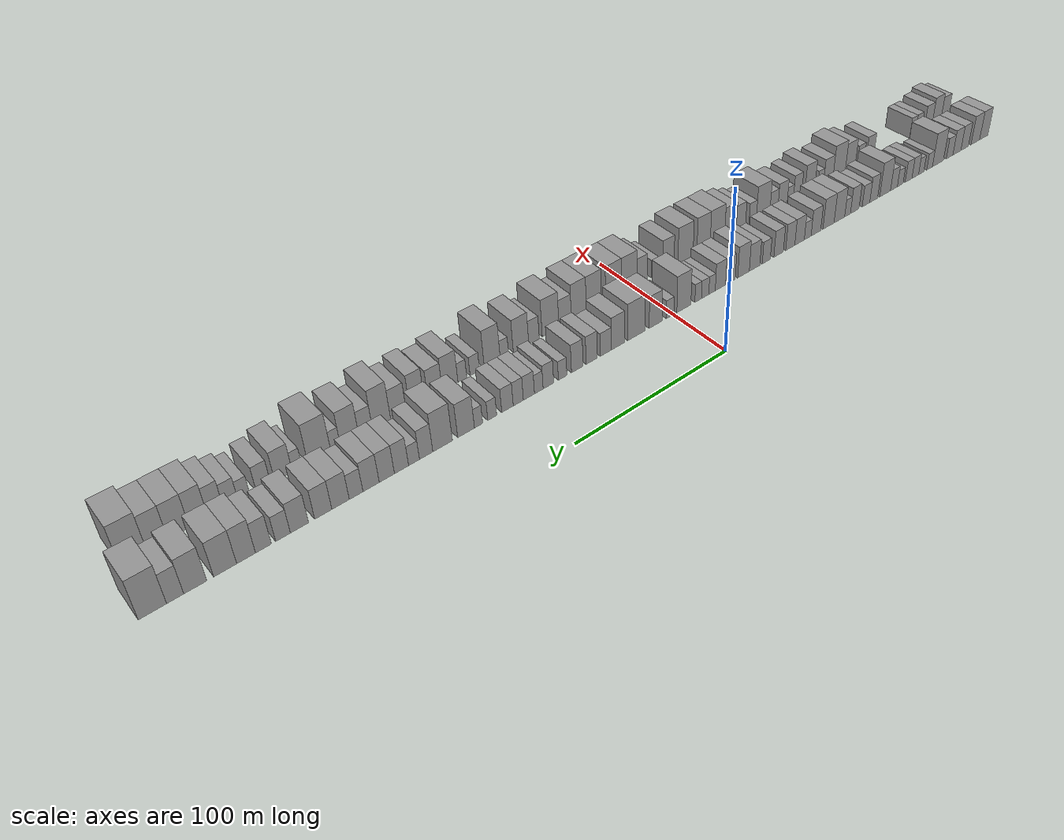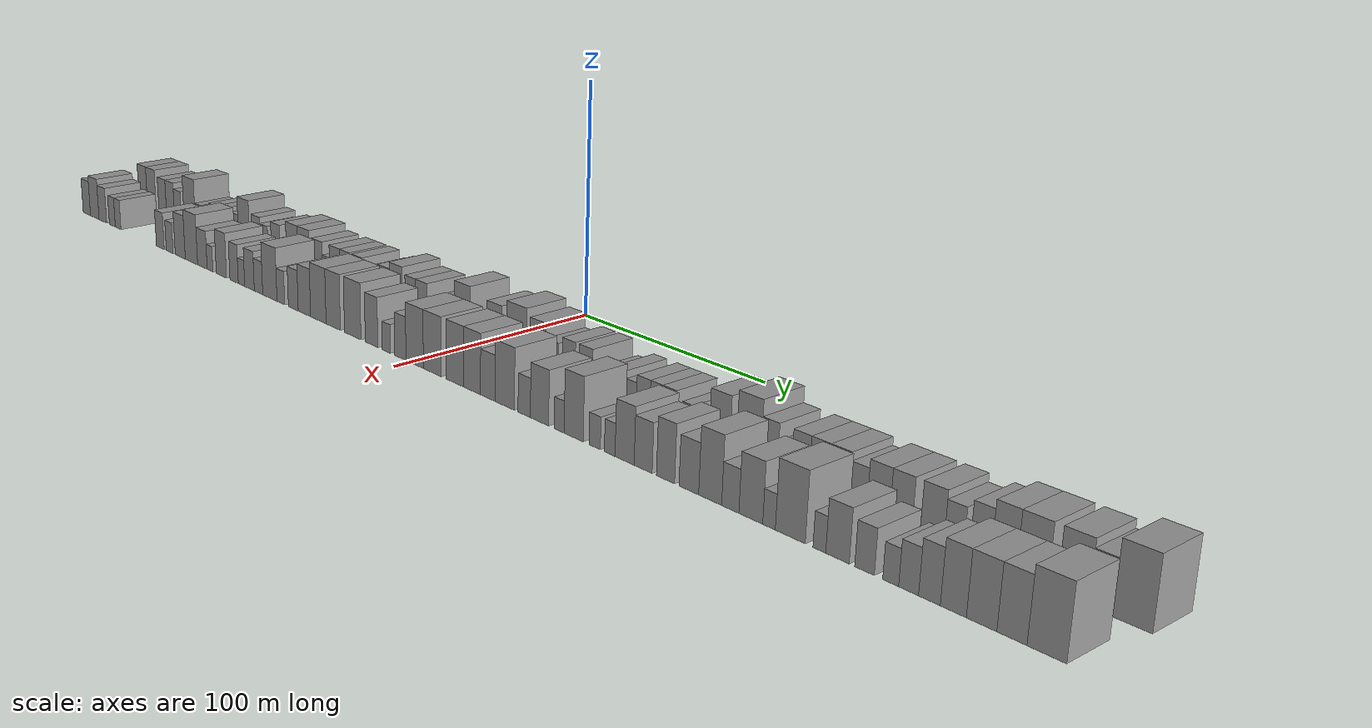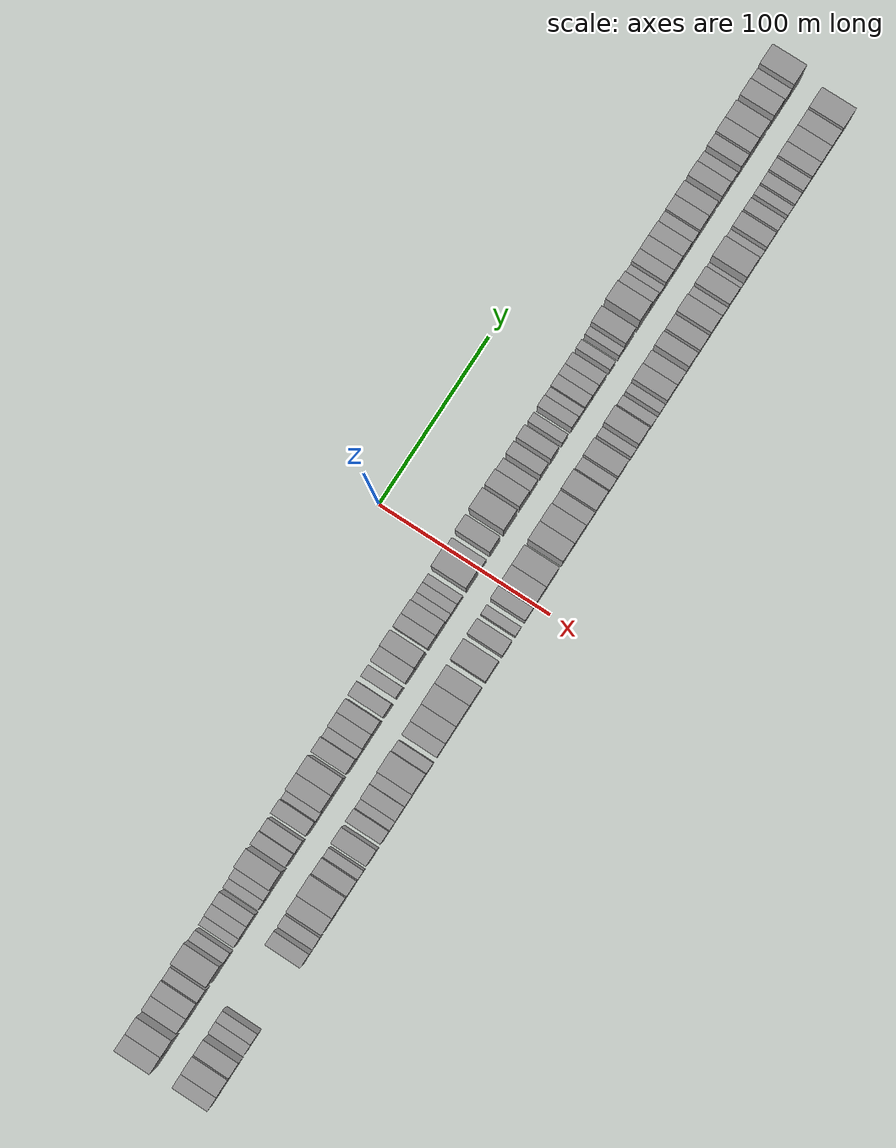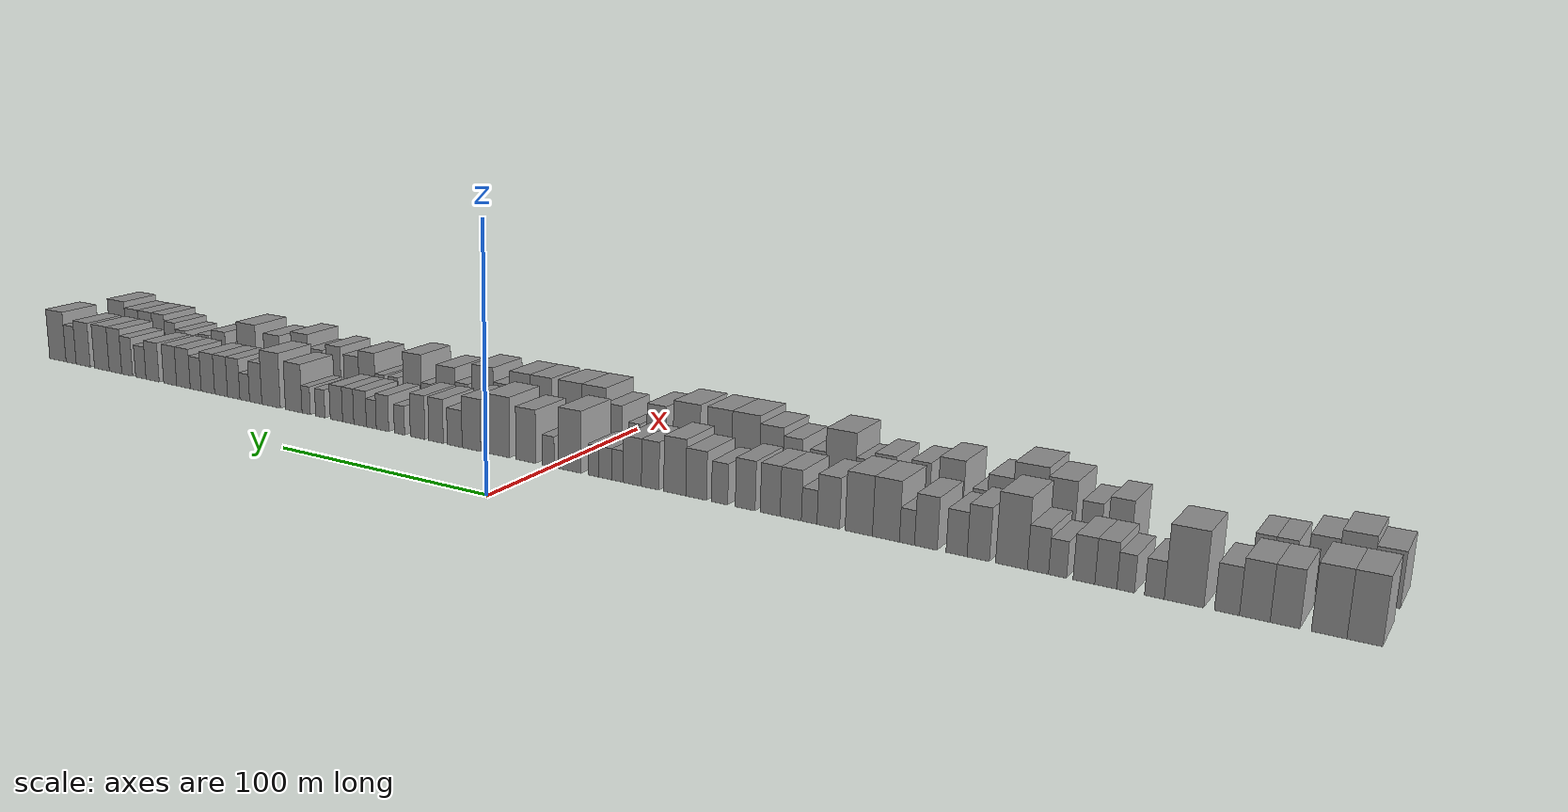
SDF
<sdf version="1.6">
 <world name="default">
  <scene>
   <sky><clouds><speed>12</speed></clouds></sky>
   <ambient>0.4 0.4 0.4 1</ambient>
   <background>0.7 0.7 0.7 1</background>
   <shadows>1</shadows>
  </scene>
  <gravity>0 0 -9.8066</gravity>
  <magnetic_field>6e-06 2.3e-05 -4.2e-05</magnetic_field>
  <physics default="0" name="default_physics" type="ode">
   <ode>
    <solver>
     <type>quick</type>
     <iters>10</iters>
     <sor>1.0</sor>
     <use_dynamic_moi_rescaling>0</use_dynamic_moi_rescaling>
    </solver>
    <constraints>
     <cfm>0</cfm>
     <erp>0.2</erp>
     <contact_max_correcting_vel>100</contact_max_correcting_vel>
     <contact_surface_layer>0.001</contact_surface_layer>
    </constraints>
   </ode>
   <max_step_size>0.004</max_step_size>
   <real_time_factor>1</real_time_factor>
   <real_time_update_rate>250</real_time_update_rate>
  </physics>
  <light name="sun" type="directional">
   <pose>0 0 10 0 0 0</pose>
   <diffuse>0.8 0.8 0.8 1</diffuse>
   <specular>0.2 0.2 0.2 1</specular>
   <attenuation>
    <range>1000</range>
    <constant>0.9</constant>
    <linear>0.01</linear>
    <quadratic>0.001</quadratic>
   </attenuation>
   <direction>-0.5 0.1 -0.9</direction>
  </light>
  <model name="building_1">
   <static>1</static>
   <pose>50.0000 -279.3835 0 0.000000 0.000000 0.000000</pose>
   <link name="link">
    <pose>0 0 10.50 0 0 0</pose>
    <collision name="collision"><geometry><box><size>20.0000 9.2331 21.0000</size></box></geometry></collision>
    <visual name="visual">
     <cast_shadows>0</cast_shadows>
     <geometry><box><size>20.0000 9.2331 21.0000</size></box></geometry>
     <material>
      <script>
       <uri>model://grey_wall/materials/scripts</uri>
       <uri>model://grey_wall/materials/textures</uri>
       <name>vrc/grey_wall</name>
      </script>
     </material>
    </visual>
   </link>
  </model>
  <model name="building_2">
   <static>1</static>
   <pose>50.0000 -270.1055 0 0.000000 0.000000 0.000000</pose>
   <link name="link">
    <pose>0 0 10.50 0 0 0</pose>
    <collision name="collision"><geometry><box><size>20.0000 9.3228 21.0000</size></box></geometry></collision>
    <visual name="visual">
     <cast_shadows>0</cast_shadows>
     <geometry><box><size>20.0000 9.3228 21.0000</size></box></geometry>
     <material>
      <script>
       <uri>model://grey_wall/materials/scripts</uri>
       <uri>model://grey_wall/materials/textures</uri>
       <name>vrc/grey_wall</name>
      </script>
     </material>
    </visual>
   </link>
  </model>
  <model name="building_3">
   <static>1</static>
   <pose>50.0000 -258.4079 0 0.000000 0.000000 0.000000</pose>
   <link name="link">
    <pose>0 0 9.00 0 0 0</pose>
    <collision name="collision"><geometry><box><size>20.0000 8.0726 18.0000</size></box></geometry></collision>
    <visual name="visual">
     <cast_shadows>0</cast_shadows>
     <geometry><box><size>20.0000 8.0726 18.0000</size></box></geometry>
     <material>
      <script>
       <uri>model://grey_wall/materials/scripts</uri>
       <uri>model://grey_wall/materials/textures</uri>
       <name>vrc/grey_wall</name>
      </script>
     </material>
    </visual>
   </link>
  </model>
  <model name="building_4">
   <static>1</static>
   <pose>50.0000 -250.1520 0 0.000000 0.000000 0.000000</pose>
   <link name="link">
    <pose>0 0 9.00 0 0 0</pose>
    <collision name="collision"><geometry><box><size>20.0000 8.4391 18.0000</size></box></geometry></collision>
    <visual name="visual">
     <cast_shadows>0</cast_shadows>
     <geometry><box><size>20.0000 8.4391 18.0000</size></box></geometry>
     <material>
      <script>
       <uri>model://grey_wall/materials/scripts</uri>
       <uri>model://grey_wall/materials/textures</uri>
       <name>vrc/grey_wall</name>
      </script>
     </material>
    </visual>
   </link>
  </model>
  <model name="building_5">
   <static>1</static>
   <pose>50.0000 -242.4353 0 0.000000 0.000000 0.000000</pose>
   <link name="link">
    <pose>0 0 7.50 0 0 0</pose>
    <collision name="collision"><geometry><box><size>20.0000 6.9945 15.0000</size></box></geometry></collision>
    <visual name="visual">
     <cast_shadows>0</cast_shadows>
     <geometry><box><size>20.0000 6.9945 15.0000</size></box></geometry>
     <material>
      <script>
       <uri>model://grey_wall/materials/scripts</uri>
       <uri>model://grey_wall/materials/textures</uri>
       <name>vrc/grey_wall</name>
      </script>
     </material>
    </visual>
   </link>
  </model>
  <model name="building_6">
   <static>1</static>
   <pose>50.0000 -230.2400 0 0.000000 0.000000 0.000000</pose>
   <link name="link">
    <pose>0 0 12.00 0 0 0</pose>
    <collision name="collision"><geometry><box><size>20.0000 11.3961 24.0000</size></box></geometry></collision>
    <visual name="visual">
     <cast_shadows>0</cast_shadows>
     <geometry><box><size>20.0000 11.3961 24.0000</size></box></geometry>
     <material>
      <script>
       <uri>model://grey_wall/materials/scripts</uri>
       <uri>model://grey_wall/materials/textures</uri>
       <name>vrc/grey_wall</name>
      </script>
     </material>
    </visual>
   </link>
  </model>
  <model name="building_7">
   <static>1</static>
   <pose>50.0000 -221.6460 0 0.000000 0.000000 0.000000</pose>
   <link name="link">
    <pose>0 0 6.00 0 0 0</pose>
    <collision name="collision"><geometry><box><size>20.0000 5.7920 12.0000</size></box></geometry></collision>
    <visual name="visual">
     <cast_shadows>0</cast_shadows>
     <geometry><box><size>20.0000 5.7920 12.0000</size></box></geometry>
     <material>
      <script>
       <uri>model://grey_wall/materials/scripts</uri>
       <uri>model://grey_wall/materials/textures</uri>
       <name>vrc/grey_wall</name>
      </script>
     </material>
    </visual>
   </link>
  </model>
  <model name="building_8">
   <static>1</static>
   <pose>50.0000 -213.1121 0 0.000000 0.000000 0.000000</pose>
   <link name="link">
    <pose>0 0 6.00 0 0 0</pose>
    <collision name="collision"><geometry><box><size>20.0000 5.2758 12.0000</size></box></geometry></collision>
    <visual name="visual">
     <cast_shadows>0</cast_shadows>
     <geometry><box><size>20.0000 5.2758 12.0000</size></box></geometry>
     <material>
      <script>
       <uri>model://grey_wall/materials/scripts</uri>
       <uri>model://grey_wall/materials/textures</uri>
       <name>vrc/grey_wall</name>
      </script>
     </material>
    </visual>
   </link>
  </model>
  <model name="building_9">
   <static>1</static>
   <pose>50.0000 -207.1385 0 0.000000 0.000000 0.000000</pose>
   <link name="link">
    <pose>0 0 7.50 0 0 0</pose>
    <collision name="collision"><geometry><box><size>20.0000 6.6714 15.0000</size></box></geometry></collision>
    <visual name="visual">
     <cast_shadows>0</cast_shadows>
     <geometry><box><size>20.0000 6.6714 15.0000</size></box></geometry>
     <material>
      <script>
       <uri>model://grey_wall/materials/scripts</uri>
       <uri>model://grey_wall/materials/textures</uri>
       <name>vrc/grey_wall</name>
      </script>
     </material>
    </visual>
   </link>
  </model>
  <model name="building_10">
   <static>1</static>
   <pose>50.0000 -200.4387 0 0.000000 0.000000 0.000000</pose>
   <link name="link">
    <pose>0 0 7.50 0 0 0</pose>
    <collision name="collision"><geometry><box><size>20.0000 6.7280 15.0000</size></box></geometry></collision>
    <visual name="visual">
     <cast_shadows>0</cast_shadows>
     <geometry><box><size>20.0000 6.7280 15.0000</size></box></geometry>
     <material>
      <script>
       <uri>model://grey_wall/materials/scripts</uri>
       <uri>model://grey_wall/materials/textures</uri>
       <name>vrc/grey_wall</name>
      </script>
     </material>
    </visual>
   </link>
  </model>
  <model name="building_11">
   <static>1</static>
   <pose>50.0000 -192.2486 0 0.000000 0.000000 0.000000</pose>
   <link name="link">
    <pose>0 0 6.00 0 0 0</pose>
    <collision name="collision"><geometry><box><size>20.0000 5.6523 12.0000</size></box></geometry></collision>
    <visual name="visual">
     <cast_shadows>0</cast_shadows>
     <geometry><box><size>20.0000 5.6523 12.0000</size></box></geometry>
     <material>
      <script>
       <uri>model://grey_wall/materials/scripts</uri>
       <uri>model://grey_wall/materials/textures</uri>
       <name>vrc/grey_wall</name>
      </script>
     </material>
    </visual>
   </link>
  </model>
  <model name="building_12">
   <static>1</static>
   <pose>50.0000 -186.0537 0 0.000000 0.000000 0.000000</pose>
   <link name="link">
    <pose>0 0 7.50 0 0 0</pose>
    <collision name="collision"><geometry><box><size>20.0000 6.7374 15.0000</size></box></geometry></collision>
    <visual name="visual">
     <cast_shadows>0</cast_shadows>
     <geometry><box><size>20.0000 6.7374 15.0000</size></box></geometry>
     <material>
      <script>
       <uri>model://grey_wall/materials/scripts</uri>
       <uri>model://grey_wall/materials/textures</uri>
       <name>vrc/grey_wall</name>
      </script>
     </material>
    </visual>
   </link>
  </model>
  <model name="building_13">
   <static>1</static>
   <pose>50.0000 -177.5244 0 0.000000 0.000000 0.000000</pose>
   <link name="link">
    <pose>0 0 12.00 0 0 0</pose>
    <collision name="collision"><geometry><box><size>20.0000 10.3212 24.0000</size></box></geometry></collision>
    <visual name="visual">
     <cast_shadows>0</cast_shadows>
     <geometry><box><size>20.0000 10.3212 24.0000</size></box></geometry>
     <material>
      <script>
       <uri>model://grey_wall/materials/scripts</uri>
       <uri>model://grey_wall/materials/textures</uri>
       <name>vrc/grey_wall</name>
      </script>
     </material>
    </visual>
   </link>
  </model>
  <model name="building_14">
   <static>1</static>
   <pose>50.0000 -166.6423 0 0.000000 0.000000 0.000000</pose>
   <link name="link">
    <pose>0 0 9.00 0 0 0</pose>
    <collision name="collision"><geometry><box><size>20.0000 7.4430 18.0000</size></box></geometry></collision>
    <visual name="visual">
     <cast_shadows>0</cast_shadows>
     <geometry><box><size>20.0000 7.4430 18.0000</size></box></geometry>
     <material>
      <script>
       <uri>model://grey_wall/materials/scripts</uri>
       <uri>model://grey_wall/materials/textures</uri>
       <name>vrc/grey_wall</name>
      </script>
     </material>
    </visual>
   </link>
  </model>
  <model name="building_15">
   <static>1</static>
   <pose>50.0000 -159.3903 0 0.000000 0.000000 0.000000</pose>
   <link name="link">
    <pose>0 0 7.50 0 0 0</pose>
    <collision name="collision"><geometry><box><size>20.0000 7.0609 15.0000</size></box></geometry></collision>
    <visual name="visual">
     <cast_shadows>0</cast_shadows>
     <geometry><box><size>20.0000 7.0609 15.0000</size></box></geometry>
     <material>
      <script>
       <uri>model://grey_wall/materials/scripts</uri>
       <uri>model://grey_wall/materials/textures</uri>
       <name>vrc/grey_wall</name>
      </script>
     </material>
    </visual>
   </link>
  </model>
  <model name="building_16">
   <static>1</static>
   <pose>50.0000 -148.9414 0 0.000000 0.000000 0.000000</pose>
   <link name="link">
    <pose>0 0 9.00 0 0 0</pose>
    <collision name="collision"><geometry><box><size>20.0000 7.8368 18.0000</size></box></geometry></collision>
    <visual name="visual">
     <cast_shadows>0</cast_shadows>
     <geometry><box><size>20.0000 7.8368 18.0000</size></box></geometry>
     <material>
      <script>
       <uri>model://grey_wall/materials/scripts</uri>
       <uri>model://grey_wall/materials/textures</uri>
       <name>vrc/grey_wall</name>
      </script>
     </material>
    </visual>
   </link>
  </model>
  <model name="building_17">
   <static>1</static>
   <pose>50.0000 -142.3813 0 0.000000 0.000000 0.000000</pose>
   <link name="link">
    <pose>0 0 6.00 0 0 0</pose>
    <collision name="collision"><geometry><box><size>20.0000 5.2835 12.0000</size></box></geometry></collision>
    <visual name="visual">
     <cast_shadows>0</cast_shadows>
     <geometry><box><size>20.0000 5.2835 12.0000</size></box></geometry>
     <material>
      <script>
       <uri>model://grey_wall/materials/scripts</uri>
       <uri>model://grey_wall/materials/textures</uri>
       <name>vrc/grey_wall</name>
      </script>
     </material>
    </visual>
   </link>
  </model>
  <model name="building_18">
   <static>1</static>
   <pose>50.0000 -134.9490 0 0.000000 0.000000 0.000000</pose>
   <link name="link">
    <pose>0 0 10.50 0 0 0</pose>
    <collision name="collision"><geometry><box><size>20.0000 9.5811 21.0000</size></box></geometry></collision>
    <visual name="visual">
     <cast_shadows>0</cast_shadows>
     <geometry><box><size>20.0000 9.5811 21.0000</size></box></geometry>
     <material>
      <script>
       <uri>model://grey_wall/materials/scripts</uri>
       <uri>model://grey_wall/materials/textures</uri>
       <name>vrc/grey_wall</name>
      </script>
     </material>
    </visual>
   </link>
  </model>
  <model name="building_19">
   <static>1</static>
   <pose>50.0000 -125.2117 0 0.000000 0.000000 0.000000</pose>
   <link name="link">
    <pose>0 0 10.50 0 0 0</pose>
    <collision name="collision"><geometry><box><size>20.0000 9.8934 21.0000</size></box></geometry></collision>
    <visual name="visual">
     <cast_shadows>0</cast_shadows>
     <geometry><box><size>20.0000 9.8934 21.0000</size></box></geometry>
     <material>
      <script>
       <uri>model://grey_wall/materials/scripts</uri>
       <uri>model://grey_wall/materials/textures</uri>
       <name>vrc/grey_wall</name>
      </script>
     </material>
    </visual>
   </link>
  </model>
  <model name="building_20">
   <static>1</static>
   <pose>50.0000 -114.0749 0 0.000000 0.000000 0.000000</pose>
   <link name="link">
    <pose>0 0 9.00 0 0 0</pose>
    <collision name="collision"><geometry><box><size>20.0000 8.3802 18.0000</size></box></geometry></collision>
    <visual name="visual">
     <cast_shadows>0</cast_shadows>
     <geometry><box><size>20.0000 8.3802 18.0000</size></box></geometry>
     <material>
      <script>
       <uri>model://grey_wall/materials/scripts</uri>
       <uri>model://grey_wall/materials/textures</uri>
       <name>vrc/grey_wall</name>
      </script>
     </material>
    </visual>
   </link>
  </model>
  <model name="building_21">
   <static>1</static>
   <pose>50.0000 -106.9440 0 0.000000 0.000000 0.000000</pose>
   <link name="link">
    <pose>0 0 6.00 0 0 0</pose>
    <collision name="collision"><geometry><box><size>20.0000 5.8816 12.0000</size></box></geometry></collision>
    <visual name="visual">
     <cast_shadows>0</cast_shadows>
     <geometry><box><size>20.0000 5.8816 12.0000</size></box></geometry>
     <material>
      <script>
       <uri>model://grey_wall/materials/scripts</uri>
       <uri>model://grey_wall/materials/textures</uri>
       <name>vrc/grey_wall</name>
      </script>
     </material>
    </visual>
   </link>
  </model>
  <model name="building_22">
   <static>1</static>
   <pose>50.0000 -99.9603 0 0.000000 0.000000 0.000000</pose>
   <link name="link">
    <pose>0 0 9.00 0 0 0</pose>
    <collision name="collision"><geometry><box><size>20.0000 8.0857 18.0000</size></box></geometry></collision>
    <visual name="visual">
     <cast_shadows>0</cast_shadows>
     <geometry><box><size>20.0000 8.0857 18.0000</size></box></geometry>
     <material>
      <script>
       <uri>model://grey_wall/materials/scripts</uri>
       <uri>model://grey_wall/materials/textures</uri>
       <name>vrc/grey_wall</name>
      </script>
     </material>
    </visual>
   </link>
  </model>
  <model name="building_23">
   <static>1</static>
   <pose>50.0000 -92.0587 0 0.000000 0.000000 0.000000</pose>
   <link name="link">
    <pose>0 0 9.00 0 0 0</pose>
    <collision name="collision"><geometry><box><size>20.0000 7.7175 18.0000</size></box></geometry></collision>
    <visual name="visual">
     <cast_shadows>0</cast_shadows>
     <geometry><box><size>20.0000 7.7175 18.0000</size></box></geometry>
     <material>
      <script>
       <uri>model://grey_wall/materials/scripts</uri>
       <uri>model://grey_wall/materials/textures</uri>
       <name>vrc/grey_wall</name>
      </script>
     </material>
    </visual>
   </link>
  </model>
  <model name="building_24">
   <static>1</static>
   <pose>50.0000 -82.2787 0 0.000000 0.000000 0.000000</pose>
   <link name="link">
    <pose>0 0 9.00 0 0 0</pose>
    <collision name="collision"><geometry><box><size>20.0000 7.8427 18.0000</size></box></geometry></collision>
    <visual name="visual">
     <cast_shadows>0</cast_shadows>
     <geometry><box><size>20.0000 7.8427 18.0000</size></box></geometry>
     <material>
      <script>
       <uri>model://grey_wall/materials/scripts</uri>
       <uri>model://grey_wall/materials/textures</uri>
       <name>vrc/grey_wall</name>
      </script>
     </material>
    </visual>
   </link>
  </model>
  <model name="building_25">
   <static>1</static>
   <pose>50.0000 -72.0794 0 0.000000 0.000000 0.000000</pose>
   <link name="link">
    <pose>0 0 7.50 0 0 0</pose>
    <collision name="collision"><geometry><box><size>20.0000 6.5558 15.0000</size></box></geometry></collision>
    <visual name="visual">
     <cast_shadows>0</cast_shadows>
     <geometry><box><size>20.0000 6.5558 15.0000</size></box></geometry>
     <material>
      <script>
       <uri>model://grey_wall/materials/scripts</uri>
       <uri>model://grey_wall/materials/textures</uri>
       <name>vrc/grey_wall</name>
      </script>
     </material>
    </visual>
   </link>
  </model>
  <model name="building_26">
   <static>1</static>
   <pose>50.0000 -62.5581 0 0.000000 0.000000 0.000000</pose>
   <link name="link">
    <pose>0 0 9.00 0 0 0</pose>
    <collision name="collision"><geometry><box><size>20.0000 8.4868 18.0000</size></box></geometry></collision>
    <visual name="visual">
     <cast_shadows>0</cast_shadows>
     <geometry><box><size>20.0000 8.4868 18.0000</size></box></geometry>
     <material>
      <script>
       <uri>model://grey_wall/materials/scripts</uri>
       <uri>model://grey_wall/materials/textures</uri>
       <name>vrc/grey_wall</name>
      </script>
     </material>
    </visual>
   </link>
  </model>
  <model name="building_27">
   <static>1</static>
   <pose>50.0000 -53.7057 0 0.000000 0.000000 0.000000</pose>
   <link name="link">
    <pose>0 0 10.50 0 0 0</pose>
    <collision name="collision"><geometry><box><size>20.0000 9.2180 21.0000</size></box></geometry></collision>
    <visual name="visual">
     <cast_shadows>0</cast_shadows>
     <geometry><box><size>20.0000 9.2180 21.0000</size></box></geometry>
     <material>
      <script>
       <uri>model://grey_wall/materials/scripts</uri>
       <uri>model://grey_wall/materials/textures</uri>
       <name>vrc/grey_wall</name>
      </script>
     </material>
    </visual>
   </link>
  </model>
  <model name="building_28">
   <static>1</static>
   <pose>50.0000 -43.3531 0 0.000000 0.000000 0.000000</pose>
   <link name="link">
    <pose>0 0 9.00 0 0 0</pose>
    <collision name="collision"><geometry><box><size>20.0000 7.4873 18.0000</size></box></geometry></collision>
    <visual name="visual">
     <cast_shadows>0</cast_shadows>
     <geometry><box><size>20.0000 7.4873 18.0000</size></box></geometry>
     <material>
      <script>
       <uri>model://grey_wall/materials/scripts</uri>
       <uri>model://grey_wall/materials/textures</uri>
       <name>vrc/grey_wall</name>
      </script>
     </material>
    </visual>
   </link>
  </model>
  <model name="building_29">
   <static>1</static>
   <pose>50.0000 -35.6290 0 0.000000 0.000000 0.000000</pose>
   <link name="link">
    <pose>0 0 9.00 0 0 0</pose>
    <collision name="collision"><geometry><box><size>20.0000 7.9609 18.0000</size></box></geometry></collision>
    <visual name="visual">
     <cast_shadows>0</cast_shadows>
     <geometry><box><size>20.0000 7.9609 18.0000</size></box></geometry>
     <material>
      <script>
       <uri>model://grey_wall/materials/scripts</uri>
       <uri>model://grey_wall/materials/textures</uri>
       <name>vrc/grey_wall</name>
      </script>
     </material>
    </visual>
   </link>
  </model>
  <model name="building_30">
   <static>1</static>
   <pose>50.0000 -29.1863 0 0.000000 0.000000 0.000000</pose>
   <link name="link">
    <pose>0 0 6.00 0 0 0</pose>
    <collision name="collision"><geometry><box><size>20.0000 4.9245 12.0000</size></box></geometry></collision>
    <visual name="visual">
     <cast_shadows>0</cast_shadows>
     <geometry><box><size>20.0000 4.9245 12.0000</size></box></geometry>
     <material>
      <script>
       <uri>model://grey_wall/materials/scripts</uri>
       <uri>model://grey_wall/materials/textures</uri>
       <name>vrc/grey_wall</name>
      </script>
     </material>
    </visual>
   </link>
  </model>
  <model name="building_31">
   <static>1</static>
   <pose>50.0000 -23.9347 0 0.000000 0.000000 0.000000</pose>
   <link name="link">
    <pose>0 0 6.00 0 0 0</pose>
    <collision name="collision"><geometry><box><size>20.0000 5.5786 12.0000</size></box></geometry></collision>
    <visual name="visual">
     <cast_shadows>0</cast_shadows>
     <geometry><box><size>20.0000 5.5786 12.0000</size></box></geometry>
     <material>
      <script>
       <uri>model://grey_wall/materials/scripts</uri>
       <uri>model://grey_wall/materials/textures</uri>
       <name>vrc/grey_wall</name>
      </script>
     </material>
    </visual>
   </link>
  </model>
  <model name="building_32">
   <static>1</static>
   <pose>50.0000 -18.6624 0 0.000000 0.000000 0.000000</pose>
   <link name="link">
    <pose>0 0 6.00 0 0 0</pose>
    <collision name="collision"><geometry><box><size>20.0000 4.9661 12.0000</size></box></geometry></collision>
    <visual name="visual">
     <cast_shadows>0</cast_shadows>
     <geometry><box><size>20.0000 4.9661 12.0000</size></box></geometry>
     <material>
      <script>
       <uri>model://grey_wall/materials/scripts</uri>
       <uri>model://grey_wall/materials/textures</uri>
       <name>vrc/grey_wall</name>
      </script>
     </material>
    </visual>
   </link>
  </model>
  <model name="building_33">
   <static>1</static>
   <pose>50.0000 -8.0052 0 0.000000 0.000000 0.000000</pose>
   <link name="link">
    <pose>0 0 12.00 0 0 0</pose>
    <collision name="collision"><geometry><box><size>20.0000 10.3484 24.0000</size></box></geometry></collision>
    <visual name="visual">
     <cast_shadows>0</cast_shadows>
     <geometry><box><size>20.0000 10.3484 24.0000</size></box></geometry>
     <material>
      <script>
       <uri>model://grey_wall/materials/scripts</uri>
       <uri>model://grey_wall/materials/textures</uri>
       <name>vrc/grey_wall</name>
      </script>
     </material>
    </visual>
   </link>
  </model>
  <model name="building_34">
   <static>1</static>
   <pose>50.0000 1.9745 0 0.000000 0.000000 0.000000</pose>
   <link name="link">
    <pose>0 0 6.00 0 0 0</pose>
    <collision name="collision"><geometry><box><size>20.0000 5.6110 12.0000</size></box></geometry></collision>
    <visual name="visual">
     <cast_shadows>0</cast_shadows>
     <geometry><box><size>20.0000 5.6110 12.0000</size></box></geometry>
     <material>
      <script>
       <uri>model://grey_wall/materials/scripts</uri>
       <uri>model://grey_wall/materials/textures</uri>
       <name>vrc/grey_wall</name>
      </script>
     </material>
    </visual>
   </link>
  </model>
  <model name="building_35">
   <static>1</static>
   <pose>50.0000 12.4085 0 0.000000 0.000000 0.000000</pose>
   <link name="link">
    <pose>0 0 10.50 0 0 0</pose>
    <collision name="collision"><geometry><box><size>20.0000 9.2569 21.0000</size></box></geometry></collision>
    <visual name="visual">
     <cast_shadows>0</cast_shadows>
     <geometry><box><size>20.0000 9.2569 21.0000</size></box></geometry>
     <material>
      <script>
       <uri>model://grey_wall/materials/scripts</uri>
       <uri>model://grey_wall/materials/textures</uri>
       <name>vrc/grey_wall</name>
      </script>
     </material>
    </visual>
   </link>
  </model>
  <model name="building_36">
   <static>1</static>
   <pose>50.0000 26.0304 0 0.000000 0.000000 0.000000</pose>
   <link name="link">
    <pose>0 0 12.00 0 0 0</pose>
    <collision name="collision"><geometry><box><size>20.0000 11.9869 24.0000</size></box></geometry></collision>
    <visual name="visual">
     <cast_shadows>0</cast_shadows>
     <geometry><box><size>20.0000 11.9869 24.0000</size></box></geometry>
     <material>
      <script>
       <uri>model://grey_wall/materials/scripts</uri>
       <uri>model://grey_wall/materials/textures</uri>
       <name>vrc/grey_wall</name>
      </script>
     </material>
    </visual>
   </link>
  </model>
  <model name="building_37">
   <static>1</static>
   <pose>50.0000 38.6332 0 0.000000 0.000000 0.000000</pose>
   <link name="link">
    <pose>0 0 10.50 0 0 0</pose>
    <collision name="collision"><geometry><box><size>20.0000 9.2187 21.0000</size></box></geometry></collision>
    <visual name="visual">
     <cast_shadows>0</cast_shadows>
     <geometry><box><size>20.0000 9.2187 21.0000</size></box></geometry>
     <material>
      <script>
       <uri>model://grey_wall/materials/scripts</uri>
       <uri>model://grey_wall/materials/textures</uri>
       <name>vrc/grey_wall</name>
      </script>
     </material>
    </visual>
   </link>
  </model>
  <model name="building_38">
   <static>1</static>
   <pose>50.0000 46.9688 0 0.000000 0.000000 0.000000</pose>
   <link name="link">
    <pose>0 0 7.50 0 0 0</pose>
    <collision name="collision"><geometry><box><size>20.0000 7.4526 15.0000</size></box></geometry></collision>
    <visual name="visual">
     <cast_shadows>0</cast_shadows>
     <geometry><box><size>20.0000 7.4526 15.0000</size></box></geometry>
     <material>
      <script>
       <uri>model://grey_wall/materials/scripts</uri>
       <uri>model://grey_wall/materials/textures</uri>
       <name>vrc/grey_wall</name>
      </script>
     </material>
    </visual>
   </link>
  </model>
  <model name="building_39">
   <static>1</static>
   <pose>50.0000 56.3891 0 0.000000 0.000000 0.000000</pose>
   <link name="link">
    <pose>0 0 9.00 0 0 0</pose>
    <collision name="collision"><geometry><box><size>20.0000 7.3880 18.0000</size></box></geometry></collision>
    <visual name="visual">
     <cast_shadows>0</cast_shadows>
     <geometry><box><size>20.0000 7.3880 18.0000</size></box></geometry>
     <material>
      <script>
       <uri>model://grey_wall/materials/scripts</uri>
       <uri>model://grey_wall/materials/textures</uri>
       <name>vrc/grey_wall</name>
      </script>
     </material>
    </visual>
   </link>
  </model>
  <model name="building_40">
   <static>1</static>
   <pose>50.0000 65.8690 0 0.000000 0.000000 0.000000</pose>
   <link name="link">
    <pose>0 0 9.00 0 0 0</pose>
    <collision name="collision"><geometry><box><size>20.0000 7.5716 18.0000</size></box></geometry></collision>
    <visual name="visual">
     <cast_shadows>0</cast_shadows>
     <geometry><box><size>20.0000 7.5716 18.0000</size></box></geometry>
     <material>
      <script>
       <uri>model://grey_wall/materials/scripts</uri>
       <uri>model://grey_wall/materials/textures</uri>
       <name>vrc/grey_wall</name>
      </script>
     </material>
    </visual>
   </link>
  </model>
  <model name="building_41">
   <static>1</static>
   <pose>50.0000 75.3594 0 0.000000 0.000000 0.000000</pose>
   <link name="link">
    <pose>0 0 6.00 0 0 0</pose>
    <collision name="collision"><geometry><box><size>20.0000 5.4093 12.0000</size></box></geometry></collision>
    <visual name="visual">
     <cast_shadows>0</cast_shadows>
     <geometry><box><size>20.0000 5.4093 12.0000</size></box></geometry>
     <material>
      <script>
       <uri>model://grey_wall/materials/scripts</uri>
       <uri>model://grey_wall/materials/textures</uri>
       <name>vrc/grey_wall</name>
      </script>
     </material>
    </visual>
   </link>
  </model>
  <model name="building_42">
   <static>1</static>
   <pose>50.0000 84.3849 0 0.000000 0.000000 0.000000</pose>
   <link name="link">
    <pose>0 0 7.50 0 0 0</pose>
    <collision name="collision"><geometry><box><size>20.0000 6.6418 15.0000</size></box></geometry></collision>
    <visual name="visual">
     <cast_shadows>0</cast_shadows>
     <geometry><box><size>20.0000 6.6418 15.0000</size></box></geometry>
     <material>
      <script>
       <uri>model://grey_wall/materials/scripts</uri>
       <uri>model://grey_wall/materials/textures</uri>
       <name>vrc/grey_wall</name>
      </script>
     </material>
    </visual>
   </link>
  </model>
  <model name="building_43">
   <static>1</static>
   <pose>50.0000 90.3973 0 0.000000 0.000000 0.000000</pose>
   <link name="link">
    <pose>0 0 6.00 0 0 0</pose>
    <collision name="collision"><geometry><box><size>20.0000 5.3829 12.0000</size></box></geometry></collision>
    <visual name="visual">
     <cast_shadows>0</cast_shadows>
     <geometry><box><size>20.0000 5.3829 12.0000</size></box></geometry>
     <material>
      <script>
       <uri>model://grey_wall/materials/scripts</uri>
       <uri>model://grey_wall/materials/textures</uri>
       <name>vrc/grey_wall</name>
      </script>
     </material>
    </visual>
   </link>
  </model>
  <model name="building_44">
   <static>1</static>
   <pose>50.0000 96.5161 0 0.000000 0.000000 0.000000</pose>
   <link name="link">
    <pose>0 0 7.50 0 0 0</pose>
    <collision name="collision"><geometry><box><size>20.0000 6.8548 15.0000</size></box></geometry></collision>
    <visual name="visual">
     <cast_shadows>0</cast_shadows>
     <geometry><box><size>20.0000 6.8548 15.0000</size></box></geometry>
     <material>
      <script>
       <uri>model://grey_wall/materials/scripts</uri>
       <uri>model://grey_wall/materials/textures</uri>
       <name>vrc/grey_wall</name>
      </script>
     </material>
    </visual>
   </link>
  </model>
  <model name="building_45">
   <static>1</static>
   <pose>50.0000 103.0263 0 0.000000 0.000000 0.000000</pose>
   <link name="link">
    <pose>0 0 7.50 0 0 0</pose>
    <collision name="collision"><geometry><box><size>20.0000 6.1654 15.0000</size></box></geometry></collision>
    <visual name="visual">
     <cast_shadows>0</cast_shadows>
     <geometry><box><size>20.0000 6.1654 15.0000</size></box></geometry>
     <material>
      <script>
       <uri>model://grey_wall/materials/scripts</uri>
       <uri>model://grey_wall/materials/textures</uri>
       <name>vrc/grey_wall</name>
      </script>
     </material>
    </visual>
   </link>
  </model>
  <model name="building_46">
   <static>1</static>
   <pose>50.0000 109.5577 0 0.000000 0.000000 0.000000</pose>
   <link name="link">
    <pose>0 0 7.50 0 0 0</pose>
    <collision name="collision"><geometry><box><size>20.0000 6.8975 15.0000</size></box></geometry></collision>
    <visual name="visual">
     <cast_shadows>0</cast_shadows>
     <geometry><box><size>20.0000 6.8975 15.0000</size></box></geometry>
     <material>
      <script>
       <uri>model://grey_wall/materials/scripts</uri>
       <uri>model://grey_wall/materials/textures</uri>
       <name>vrc/grey_wall</name>
      </script>
     </material>
    </visual>
   </link>
  </model>
  <model name="building_47">
   <static>1</static>
   <pose>50.0000 118.6466 0 0.000000 0.000000 0.000000</pose>
   <link name="link">
    <pose>0 0 6.00 0 0 0</pose>
    <collision name="collision"><geometry><box><size>20.0000 5.2803 12.0000</size></box></geometry></collision>
    <visual name="visual">
     <cast_shadows>0</cast_shadows>
     <geometry><box><size>20.0000 5.2803 12.0000</size></box></geometry>
     <material>
      <script>
       <uri>model://grey_wall/materials/scripts</uri>
       <uri>model://grey_wall/materials/textures</uri>
       <name>vrc/grey_wall</name>
      </script>
     </material>
    </visual>
   </link>
  </model>
  <model name="building_48">
   <static>1</static>
   <pose>50.0000 126.6877 0 0.000000 0.000000 0.000000</pose>
   <link name="link">
    <pose>0 0 6.00 0 0 0</pose>
    <collision name="collision"><geometry><box><size>20.0000 4.8019 12.0000</size></box></geometry></collision>
    <visual name="visual">
     <cast_shadows>0</cast_shadows>
     <geometry><box><size>20.0000 4.8019 12.0000</size></box></geometry>
     <material>
      <script>
       <uri>model://grey_wall/materials/scripts</uri>
       <uri>model://grey_wall/materials/textures</uri>
       <name>vrc/grey_wall</name>
      </script>
     </material>
    </visual>
   </link>
  </model>
  <model name="building_49">
   <static>1</static>
   <pose>50.0000 133.8981 0 0.000000 0.000000 0.000000</pose>
   <link name="link">
    <pose>0 0 10.50 0 0 0</pose>
    <collision name="collision"><geometry><box><size>20.0000 9.6188 21.0000</size></box></geometry></collision>
    <visual name="visual">
     <cast_shadows>0</cast_shadows>
     <geometry><box><size>20.0000 9.6188 21.0000</size></box></geometry>
     <material>
      <script>
       <uri>model://grey_wall/materials/scripts</uri>
       <uri>model://grey_wall/materials/textures</uri>
       <name>vrc/grey_wall</name>
      </script>
     </material>
    </visual>
   </link>
  </model>
  <model name="building_50">
   <static>1</static>
   <pose>50.0000 147.2006 0 0.000000 0.000000 0.000000</pose>
   <link name="link">
    <pose>0 0 12.00 0 0 0</pose>
    <collision name="collision"><geometry><box><size>20.0000 10.9862 24.0000</size></box></geometry></collision>
    <visual name="visual">
     <cast_shadows>0</cast_shadows>
     <geometry><box><size>20.0000 10.9862 24.0000</size></box></geometry>
     <material>
      <script>
       <uri>model://grey_wall/materials/scripts</uri>
       <uri>model://grey_wall/materials/textures</uri>
       <name>vrc/grey_wall</name>
      </script>
     </material>
    </visual>
   </link>
  </model>
  <model name="building_51">
   <static>1</static>
   <pose>50.0000 156.3773 0 0.000000 0.000000 0.000000</pose>
   <link name="link">
    <pose>0 0 9.00 0 0 0</pose>
    <collision name="collision"><geometry><box><size>20.0000 7.3672 18.0000</size></box></geometry></collision>
    <visual name="visual">
     <cast_shadows>0</cast_shadows>
     <geometry><box><size>20.0000 7.3672 18.0000</size></box></geometry>
     <material>
      <script>
       <uri>model://grey_wall/materials/scripts</uri>
       <uri>model://grey_wall/materials/textures</uri>
       <name>vrc/grey_wall</name>
      </script>
     </material>
    </visual>
   </link>
  </model>
  <model name="building_52">
   <static>1</static>
   <pose>50.0000 163.0314 0 0.000000 0.000000 0.000000</pose>
   <link name="link">
    <pose>0 0 6.00 0 0 0</pose>
    <collision name="collision"><geometry><box><size>20.0000 5.9410 12.0000</size></box></geometry></collision>
    <visual name="visual">
     <cast_shadows>0</cast_shadows>
     <geometry><box><size>20.0000 5.9410 12.0000</size></box></geometry>
     <material>
      <script>
       <uri>model://grey_wall/materials/scripts</uri>
       <uri>model://grey_wall/materials/textures</uri>
       <name>vrc/grey_wall</name>
      </script>
     </material>
    </visual>
   </link>
  </model>
  <model name="building_53">
   <static>1</static>
   <pose>50.0000 169.7892 0 0.000000 0.000000 0.000000</pose>
   <link name="link">
    <pose>0 0 9.00 0 0 0</pose>
    <collision name="collision"><geometry><box><size>20.0000 7.5745 18.0000</size></box></geometry></collision>
    <visual name="visual">
     <cast_shadows>0</cast_shadows>
     <geometry><box><size>20.0000 7.5745 18.0000</size></box></geometry>
     <material>
      <script>
       <uri>model://grey_wall/materials/scripts</uri>
       <uri>model://grey_wall/materials/textures</uri>
       <name>vrc/grey_wall</name>
      </script>
     </material>
    </visual>
   </link>
  </model>
  <model name="building_54">
   <static>1</static>
   <pose>50.0000 177.5934 0 0.000000 0.000000 0.000000</pose>
   <link name="link">
    <pose>0 0 9.00 0 0 0</pose>
    <collision name="collision"><geometry><box><size>20.0000 8.0339 18.0000</size></box></geometry></collision>
    <visual name="visual">
     <cast_shadows>0</cast_shadows>
     <geometry><box><size>20.0000 8.0339 18.0000</size></box></geometry>
     <material>
      <script>
       <uri>model://grey_wall/materials/scripts</uri>
       <uri>model://grey_wall/materials/textures</uri>
       <name>vrc/grey_wall</name>
      </script>
     </material>
    </visual>
   </link>
  </model>
  <model name="building_55">
   <static>1</static>
   <pose>50.0000 185.8475 0 0.000000 0.000000 0.000000</pose>
   <link name="link">
    <pose>0 0 9.00 0 0 0</pose>
    <collision name="collision"><geometry><box><size>20.0000 8.4742 18.0000</size></box></geometry></collision>
    <visual name="visual">
     <cast_shadows>0</cast_shadows>
     <geometry><box><size>20.0000 8.4742 18.0000</size></box></geometry>
     <material>
      <script>
       <uri>model://grey_wall/materials/scripts</uri>
       <uri>model://grey_wall/materials/textures</uri>
       <name>vrc/grey_wall</name>
      </script>
     </material>
    </visual>
   </link>
  </model>
  <model name="building_56">
   <static>1</static>
   <pose>50.0000 193.5864 0 0.000000 0.000000 0.000000</pose>
   <link name="link">
    <pose>0 0 7.50 0 0 0</pose>
    <collision name="collision"><geometry><box><size>20.0000 7.0035 15.0000</size></box></geometry></collision>
    <visual name="visual">
     <cast_shadows>0</cast_shadows>
     <geometry><box><size>20.0000 7.0035 15.0000</size></box></geometry>
     <material>
      <script>
       <uri>model://grey_wall/materials/scripts</uri>
       <uri>model://grey_wall/materials/textures</uri>
       <name>vrc/grey_wall</name>
      </script>
     </material>
    </visual>
   </link>
  </model>
  <model name="building_57">
   <static>1</static>
   <pose>50.0000 201.4787 0 0.000000 0.000000 0.000000</pose>
   <link name="link">
    <pose>0 0 9.00 0 0 0</pose>
    <collision name="collision"><geometry><box><size>20.0000 8.7810 18.0000</size></box></geometry></collision>
    <visual name="visual">
     <cast_shadows>0</cast_shadows>
     <geometry><box><size>20.0000 8.7810 18.0000</size></box></geometry>
     <material>
      <script>
       <uri>model://grey_wall/materials/scripts</uri>
       <uri>model://grey_wall/materials/textures</uri>
       <name>vrc/grey_wall</name>
      </script>
     </material>
    </visual>
   </link>
  </model>
  <model name="building_58">
   <static>1</static>
   <pose>50.0000 210.1303 0 0.000000 0.000000 0.000000</pose>
   <link name="link">
    <pose>0 0 9.00 0 0 0</pose>
    <collision name="collision"><geometry><box><size>20.0000 8.5223 18.0000</size></box></geometry></collision>
    <visual name="visual">
     <cast_shadows>0</cast_shadows>
     <geometry><box><size>20.0000 8.5223 18.0000</size></box></geometry>
     <material>
      <script>
       <uri>model://grey_wall/materials/scripts</uri>
       <uri>model://grey_wall/materials/textures</uri>
       <name>vrc/grey_wall</name>
      </script>
     </material>
    </visual>
   </link>
  </model>
  <model name="building_59">
   <static>1</static>
   <pose>50.0000 221.7778 0 0.000000 0.000000 0.000000</pose>
   <link name="link">
    <pose>0 0 9.00 0 0 0</pose>
    <collision name="collision"><geometry><box><size>20.0000 8.7728 18.0000</size></box></geometry></collision>
    <visual name="visual">
     <cast_shadows>0</cast_shadows>
     <geometry><box><size>20.0000 8.7728 18.0000</size></box></geometry>
     <material>
      <script>
       <uri>model://grey_wall/materials/scripts</uri>
       <uri>model://grey_wall/materials/textures</uri>
       <name>vrc/grey_wall</name>
      </script>
     </material>
    </visual>
   </link>
  </model>
  <model name="building_60">
   <static>1</static>
   <pose>50.0000 229.6762 0 0.000000 0.000000 0.000000</pose>
   <link name="link">
    <pose>0 0 7.50 0 0 0</pose>
    <collision name="collision"><geometry><box><size>20.0000 7.0239 15.0000</size></box></geometry></collision>
    <visual name="visual">
     <cast_shadows>0</cast_shadows>
     <geometry><box><size>20.0000 7.0239 15.0000</size></box></geometry>
     <material>
      <script>
       <uri>model://grey_wall/materials/scripts</uri>
       <uri>model://grey_wall/materials/textures</uri>
       <name>vrc/grey_wall</name>
      </script>
     </material>
    </visual>
   </link>
  </model>
  <model name="building_61">
   <static>1</static>
   <pose>50.0000 238.8993 0 0.000000 0.000000 0.000000</pose>
   <link name="link">
    <pose>0 0 9.00 0 0 0</pose>
    <collision name="collision"><geometry><box><size>20.0000 7.4224 18.0000</size></box></geometry></collision>
    <visual name="visual">
     <cast_shadows>0</cast_shadows>
     <geometry><box><size>20.0000 7.4224 18.0000</size></box></geometry>
     <material>
      <script>
       <uri>model://grey_wall/materials/scripts</uri>
       <uri>model://grey_wall/materials/textures</uri>
       <name>vrc/grey_wall</name>
      </script>
     </material>
    </visual>
   </link>
  </model>
  <model name="building_62">
   <static>1</static>
   <pose>50.0000 246.9462 0 0.000000 0.000000 0.000000</pose>
   <link name="link">
    <pose>0 0 10.50 0 0 0</pose>
    <collision name="collision"><geometry><box><size>20.0000 8.6713 21.0000</size></box></geometry></collision>
    <visual name="visual">
     <cast_shadows>0</cast_shadows>
     <geometry><box><size>20.0000 8.6713 21.0000</size></box></geometry>
     <material>
      <script>
       <uri>model://grey_wall/materials/scripts</uri>
       <uri>model://grey_wall/materials/textures</uri>
       <name>vrc/grey_wall</name>
      </script>
     </material>
    </visual>
   </link>
  </model>
  <model name="building_63">
   <static>1</static>
   <pose>50.0000 256.4718 0 0.000000 0.000000 0.000000</pose>
   <link name="link">
    <pose>0 0 10.50 0 0 0</pose>
    <collision name="collision"><geometry><box><size>20.0000 10.3799 21.0000</size></box></geometry></collision>
    <visual name="visual">
     <cast_shadows>0</cast_shadows>
     <geometry><box><size>20.0000 10.3799 21.0000</size></box></geometry>
     <material>
      <script>
       <uri>model://grey_wall/materials/scripts</uri>
       <uri>model://grey_wall/materials/textures</uri>
       <name>vrc/grey_wall</name>
      </script>
     </material>
    </visual>
   </link>
  </model>
  <model name="building_64">
   <static>1</static>
   <pose>50.0000 269.7114 0 0.000000 0.000000 0.000000</pose>
   <link name="link">
    <pose>0 0 10.50 0 0 0</pose>
    <collision name="collision"><geometry><box><size>20.0000 10.0992 21.0000</size></box></geometry></collision>
    <visual name="visual">
     <cast_shadows>0</cast_shadows>
     <geometry><box><size>20.0000 10.0992 21.0000</size></box></geometry>
     <material>
      <script>
       <uri>model://grey_wall/materials/scripts</uri>
       <uri>model://grey_wall/materials/textures</uri>
       <name>vrc/grey_wall</name>
      </script>
     </material>
    </visual>
   </link>
  </model>
  <model name="building_65">
   <static>1</static>
   <pose>50.0000 278.4431 0 0.000000 0.000000 0.000000</pose>
   <link name="link">
    <pose>0 0 9.00 0 0 0</pose>
    <collision name="collision"><geometry><box><size>20.0000 7.3643 18.0000</size></box></geometry></collision>
    <visual name="visual">
     <cast_shadows>0</cast_shadows>
     <geometry><box><size>20.0000 7.3643 18.0000</size></box></geometry>
     <material>
      <script>
       <uri>model://grey_wall/materials/scripts</uri>
       <uri>model://grey_wall/materials/textures</uri>
       <name>vrc/grey_wall</name>
      </script>
     </material>
    </visual>
   </link>
  </model>
  <model name="building_66">
   <static>1</static>
   <pose>50.0000 288.1061 0 0.000000 0.000000 0.000000</pose>
   <link name="link">
    <pose>0 0 12.00 0 0 0</pose>
    <collision name="collision"><geometry><box><size>20.0000 11.9617 24.0000</size></box></geometry></collision>
    <visual name="visual">
     <cast_shadows>0</cast_shadows>
     <geometry><box><size>20.0000 11.9617 24.0000</size></box></geometry>
     <material>
      <script>
       <uri>model://grey_wall/materials/scripts</uri>
       <uri>model://grey_wall/materials/textures</uri>
       <name>vrc/grey_wall</name>
      </script>
     </material>
    </visual>
   </link>
  </model>
  <model name="building_67">
   <static>1</static>
   <pose>82.0000 -279.8822 0 0.000000 0.000000 0.000000</pose>
   <link name="link">
    <pose>0 0 9.00 0 0 0</pose>
    <collision name="collision"><geometry><box><size>20.0000 8.2355 18.0000</size></box></geometry></collision>
    <visual name="visual">
     <cast_shadows>0</cast_shadows>
     <geometry><box><size>20.0000 8.2355 18.0000</size></box></geometry>
     <material>
      <script>
       <uri>model://grey_wall/materials/scripts</uri>
       <uri>model://grey_wall/materials/textures</uri>
       <name>vrc/grey_wall</name>
      </script>
     </material>
    </visual>
   </link>
  </model>
  <model name="building_68">
   <static>1</static>
   <pose>82.0000 -270.9641 0 0.000000 0.000000 0.000000</pose>
   <link name="link">
    <pose>0 0 10.50 0 0 0</pose>
    <collision name="collision"><geometry><box><size>20.0000 9.6007 21.0000</size></box></geometry></collision>
    <visual name="visual">
     <cast_shadows>0</cast_shadows>
     <geometry><box><size>20.0000 9.6007 21.0000</size></box></geometry>
     <material>
      <script>
       <uri>model://grey_wall/materials/scripts</uri>
       <uri>model://grey_wall/materials/textures</uri>
       <name>vrc/grey_wall</name>
      </script>
     </material>
    </visual>
   </link>
  </model>
  <model name="building_69">
   <static>1</static>
   <pose>82.0000 -261.9529 0 0.000000 0.000000 0.000000</pose>
   <link name="link">
    <pose>0 0 9.00 0 0 0</pose>
    <collision name="collision"><geometry><box><size>20.0000 8.4218 18.0000</size></box></geometry></collision>
    <visual name="visual">
     <cast_shadows>0</cast_shadows>
     <geometry><box><size>20.0000 8.4218 18.0000</size></box></geometry>
     <material>
      <script>
       <uri>model://grey_wall/materials/scripts</uri>
       <uri>model://grey_wall/materials/textures</uri>
       <name>vrc/grey_wall</name>
      </script>
     </material>
    </visual>
   </link>
  </model>
  <model name="building_70">
   <static>1</static>
   <pose>82.0000 -251.5233 0 0.000000 0.000000 0.000000</pose>
   <link name="link">
    <pose>0 0 7.50 0 0 0</pose>
    <collision name="collision"><geometry><box><size>20.0000 6.4374 15.0000</size></box></geometry></collision>
    <visual name="visual">
     <cast_shadows>0</cast_shadows>
     <geometry><box><size>20.0000 6.4374 15.0000</size></box></geometry>
     <material>
      <script>
       <uri>model://grey_wall/materials/scripts</uri>
       <uri>model://grey_wall/materials/textures</uri>
       <name>vrc/grey_wall</name>
      </script>
     </material>
    </visual>
   </link>
  </model>
  <model name="building_71">
   <static>1</static>
   <pose>82.0000 -245.2903 0 0.000000 0.000000 0.000000</pose>
   <link name="link">
    <pose>0 0 7.50 0 0 0</pose>
    <collision name="collision"><geometry><box><size>20.0000 6.0286 15.0000</size></box></geometry></collision>
    <visual name="visual">
     <cast_shadows>0</cast_shadows>
     <geometry><box><size>20.0000 6.0286 15.0000</size></box></geometry>
     <material>
      <script>
       <uri>model://grey_wall/materials/scripts</uri>
       <uri>model://grey_wall/materials/textures</uri>
       <name>vrc/grey_wall</name>
      </script>
     </material>
    </visual>
   </link>
  </model>
  <model name="building_72">
   <static>1</static>
   <pose>82.0000 -201.7210 0 0.000000 0.000000 0.000000</pose>
   <link name="link">
    <pose>0 0 9.00 0 0 0</pose>
    <collision name="collision"><geometry><box><size>20.0000 7.7033 18.0000</size></box></geometry></collision>
    <visual name="visual">
     <cast_shadows>0</cast_shadows>
     <geometry><box><size>20.0000 7.7033 18.0000</size></box></geometry>
     <material>
      <script>
       <uri>model://grey_wall/materials/scripts</uri>
       <uri>model://grey_wall/materials/textures</uri>
       <name>vrc/grey_wall</name>
      </script>
     </material>
    </visual>
   </link>
  </model>
  <model name="building_73">
   <static>1</static>
   <pose>82.0000 -192.5080 0 0.000000 0.000000 0.000000</pose>
   <link name="link">
    <pose>0 0 7.50 0 0 0</pose>
    <collision name="collision"><geometry><box><size>20.0000 6.7227 15.0000</size></box></geometry></collision>
    <visual name="visual">
     <cast_shadows>0</cast_shadows>
     <geometry><box><size>20.0000 6.7227 15.0000</size></box></geometry>
     <material>
      <script>
       <uri>model://grey_wall/materials/scripts</uri>
       <uri>model://grey_wall/materials/textures</uri>
       <name>vrc/grey_wall</name>
      </script>
     </material>
    </visual>
   </link>
  </model>
  <model name="building_74">
   <static>1</static>
   <pose>82.0000 -182.3361 0 0.000000 0.000000 0.000000</pose>
   <link name="link">
    <pose>0 0 10.50 0 0 0</pose>
    <collision name="collision"><geometry><box><size>20.0000 9.6213 21.0000</size></box></geometry></collision>
    <visual name="visual">
     <cast_shadows>0</cast_shadows>
     <geometry><box><size>20.0000 9.6213 21.0000</size></box></geometry>
     <material>
      <script>
       <uri>model://grey_wall/materials/scripts</uri>
       <uri>model://grey_wall/materials/textures</uri>
       <name>vrc/grey_wall</name>
      </script>
     </material>
    </visual>
   </link>
  </model>
  <model name="building_75">
   <static>1</static>
   <pose>82.0000 -171.7310 0 0.000000 0.000000 0.000000</pose>
   <link name="link">
    <pose>0 0 12.00 0 0 0</pose>
    <collision name="collision"><geometry><box><size>20.0000 11.5889 24.0000</size></box></geometry></collision>
    <visual name="visual">
     <cast_shadows>0</cast_shadows>
     <geometry><box><size>20.0000 11.5889 24.0000</size></box></geometry>
     <material>
      <script>
       <uri>model://grey_wall/materials/scripts</uri>
       <uri>model://grey_wall/materials/textures</uri>
       <name>vrc/grey_wall</name>
      </script>
     </material>
    </visual>
   </link>
  </model>
  <model name="building_76">
   <static>1</static>
   <pose>82.0000 -161.5429 0 0.000000 0.000000 0.000000</pose>
   <link name="link">
    <pose>0 0 9.00 0 0 0</pose>
    <collision name="collision"><geometry><box><size>20.0000 8.7873 18.0000</size></box></geometry></collision>
    <visual name="visual">
     <cast_shadows>0</cast_shadows>
     <geometry><box><size>20.0000 8.7873 18.0000</size></box></geometry>
     <material>
      <script>
       <uri>model://grey_wall/materials/scripts</uri>
       <uri>model://grey_wall/materials/textures</uri>
       <name>vrc/grey_wall</name>
      </script>
     </material>
    </visual>
   </link>
  </model>
  <model name="building_77">
   <static>1</static>
   <pose>82.0000 -154.5434 0 0.000000 0.000000 0.000000</pose>
   <link name="link">
    <pose>0 0 6.00 0 0 0</pose>
    <collision name="collision"><geometry><box><size>20.0000 5.2117 12.0000</size></box></geometry></collision>
    <visual name="visual">
     <cast_shadows>0</cast_shadows>
     <geometry><box><size>20.0000 5.2117 12.0000</size></box></geometry>
     <material>
      <script>
       <uri>model://grey_wall/materials/scripts</uri>
       <uri>model://grey_wall/materials/textures</uri>
       <name>vrc/grey_wall</name>
      </script>
     </material>
    </visual>
   </link>
  </model>
  <model name="building_78">
   <static>1</static>
   <pose>82.0000 -144.3699 0 0.000000 0.000000 0.000000</pose>
   <link name="link">
    <pose>0 0 10.50 0 0 0</pose>
    <collision name="collision"><geometry><box><size>20.0000 9.1352 21.0000</size></box></geometry></collision>
    <visual name="visual">
     <cast_shadows>0</cast_shadows>
     <geometry><box><size>20.0000 9.1352 21.0000</size></box></geometry>
     <material>
      <script>
       <uri>model://grey_wall/materials/scripts</uri>
       <uri>model://grey_wall/materials/textures</uri>
       <name>vrc/grey_wall</name>
      </script>
     </material>
    </visual>
   </link>
  </model>
  <model name="building_79">
   <static>1</static>
   <pose>82.0000 -133.1547 0 0.000000 0.000000 0.000000</pose>
   <link name="link">
    <pose>0 0 9.00 0 0 0</pose>
    <collision name="collision"><geometry><box><size>20.0000 7.2952 18.0000</size></box></geometry></collision>
    <visual name="visual">
     <cast_shadows>0</cast_shadows>
     <geometry><box><size>20.0000 7.2952 18.0000</size></box></geometry>
     <material>
      <script>
       <uri>model://grey_wall/materials/scripts</uri>
       <uri>model://grey_wall/materials/textures</uri>
       <name>vrc/grey_wall</name>
      </script>
     </material>
    </visual>
   </link>
  </model>
  <model name="building_80">
   <static>1</static>
   <pose>82.0000 -126.7506 0 0.000000 0.000000 0.000000</pose>
   <link name="link">
    <pose>0 0 6.00 0 0 0</pose>
    <collision name="collision"><geometry><box><size>20.0000 5.5130 12.0000</size></box></geometry></collision>
    <visual name="visual">
     <cast_shadows>0</cast_shadows>
     <geometry><box><size>20.0000 5.5130 12.0000</size></box></geometry>
     <material>
      <script>
       <uri>model://grey_wall/materials/scripts</uri>
       <uri>model://grey_wall/materials/textures</uri>
       <name>vrc/grey_wall</name>
      </script>
     </material>
    </visual>
   </link>
  </model>
  <model name="building_81">
   <static>1</static>
   <pose>82.0000 -119.9399 0 0.000000 0.000000 0.000000</pose>
   <link name="link">
    <pose>0 0 9.00 0 0 0</pose>
    <collision name="collision"><geometry><box><size>20.0000 8.1084 18.0000</size></box></geometry></collision>
    <visual name="visual">
     <cast_shadows>0</cast_shadows>
     <geometry><box><size>20.0000 8.1084 18.0000</size></box></geometry>
     <material>
      <script>
       <uri>model://grey_wall/materials/scripts</uri>
       <uri>model://grey_wall/materials/textures</uri>
       <name>vrc/grey_wall</name>
      </script>
     </material>
    </visual>
   </link>
  </model>
  <model name="building_82">
   <static>1</static>
   <pose>82.0000 -112.3804 0 0.000000 0.000000 0.000000</pose>
   <link name="link">
    <pose>0 0 7.50 0 0 0</pose>
    <collision name="collision"><geometry><box><size>20.0000 7.0106 15.0000</size></box></geometry></collision>
    <visual name="visual">
     <cast_shadows>0</cast_shadows>
     <geometry><box><size>20.0000 7.0106 15.0000</size></box></geometry>
     <material>
      <script>
       <uri>model://grey_wall/materials/scripts</uri>
       <uri>model://grey_wall/materials/textures</uri>
       <name>vrc/grey_wall</name>
      </script>
     </material>
    </visual>
   </link>
  </model>
  <model name="building_83">
   <static>1</static>
   <pose>82.0000 -103.0256 0 0.000000 0.000000 0.000000</pose>
   <link name="link">
    <pose>0 0 12.00 0 0 0</pose>
    <collision name="collision"><geometry><box><size>20.0000 11.6991 24.0000</size></box></geometry></collision>
    <visual name="visual">
     <cast_shadows>0</cast_shadows>
     <geometry><box><size>20.0000 11.6991 24.0000</size></box></geometry>
     <material>
      <script>
       <uri>model://grey_wall/materials/scripts</uri>
       <uri>model://grey_wall/materials/textures</uri>
       <name>vrc/grey_wall</name>
      </script>
     </material>
    </visual>
   </link>
  </model>
  <model name="building_84">
   <static>1</static>
   <pose>82.0000 -94.0986 0 0.000000 0.000000 0.000000</pose>
   <link name="link">
    <pose>0 0 7.50 0 0 0</pose>
    <collision name="collision"><geometry><box><size>20.0000 6.1549 15.0000</size></box></geometry></collision>
    <visual name="visual">
     <cast_shadows>0</cast_shadows>
     <geometry><box><size>20.0000 6.1549 15.0000</size></box></geometry>
     <material>
      <script>
       <uri>model://grey_wall/materials/scripts</uri>
       <uri>model://grey_wall/materials/textures</uri>
       <name>vrc/grey_wall</name>
      </script>
     </material>
    </visual>
   </link>
  </model>
  <model name="building_85">
   <static>1</static>
   <pose>82.0000 -84.1501 0 0.000000 0.000000 0.000000</pose>
   <link name="link">
    <pose>0 0 9.00 0 0 0</pose>
    <collision name="collision"><geometry><box><size>20.0000 7.7421 18.0000</size></box></geometry></collision>
    <visual name="visual">
     <cast_shadows>0</cast_shadows>
     <geometry><box><size>20.0000 7.7421 18.0000</size></box></geometry>
     <material>
      <script>
       <uri>model://grey_wall/materials/scripts</uri>
       <uri>model://grey_wall/materials/textures</uri>
       <name>vrc/grey_wall</name>
      </script>
     </material>
    </visual>
   </link>
  </model>
  <model name="building_86">
   <static>1</static>
   <pose>82.0000 -75.4805 0 0.000000 0.000000 0.000000</pose>
   <link name="link">
    <pose>0 0 10.50 0 0 0</pose>
    <collision name="collision"><geometry><box><size>20.0000 9.5971 21.0000</size></box></geometry></collision>
    <visual name="visual">
     <cast_shadows>0</cast_shadows>
     <geometry><box><size>20.0000 9.5971 21.0000</size></box></geometry>
     <material>
      <script>
       <uri>model://grey_wall/materials/scripts</uri>
       <uri>model://grey_wall/materials/textures</uri>
       <name>vrc/grey_wall</name>
      </script>
     </material>
    </visual>
   </link>
  </model>
  <model name="building_87">
   <static>1</static>
   <pose>82.0000 -64.8374 0 0.000000 0.000000 0.000000</pose>
   <link name="link">
    <pose>0 0 12.00 0 0 0</pose>
    <collision name="collision"><geometry><box><size>20.0000 11.6890 24.0000</size></box></geometry></collision>
    <visual name="visual">
     <cast_shadows>0</cast_shadows>
     <geometry><box><size>20.0000 11.6890 24.0000</size></box></geometry>
     <material>
      <script>
       <uri>model://grey_wall/materials/scripts</uri>
       <uri>model://grey_wall/materials/textures</uri>
       <name>vrc/grey_wall</name>
      </script>
     </material>
    </visual>
   </link>
  </model>
  <model name="building_88">
   <static>1</static>
   <pose>82.0000 -53.7131 0 0.000000 0.000000 0.000000</pose>
   <link name="link">
    <pose>0 0 12.00 0 0 0</pose>
    <collision name="collision"><geometry><box><size>20.0000 10.5598 24.0000</size></box></geometry></collision>
    <visual name="visual">
     <cast_shadows>0</cast_shadows>
     <geometry><box><size>20.0000 10.5598 24.0000</size></box></geometry>
     <material>
      <script>
       <uri>model://grey_wall/materials/scripts</uri>
       <uri>model://grey_wall/materials/textures</uri>
       <name>vrc/grey_wall</name>
      </script>
     </material>
    </visual>
   </link>
  </model>
  <model name="building_89">
   <static>1</static>
   <pose>82.0000 -39.5381 0 0.000000 0.000000 0.000000</pose>
   <link name="link">
    <pose>0 0 12.00 0 0 0</pose>
    <collision name="collision"><geometry><box><size>20.0000 11.7902 24.0000</size></box></geometry></collision>
    <visual name="visual">
     <cast_shadows>0</cast_shadows>
     <geometry><box><size>20.0000 11.7902 24.0000</size></box></geometry>
     <material>
      <script>
       <uri>model://grey_wall/materials/scripts</uri>
       <uri>model://grey_wall/materials/textures</uri>
       <name>vrc/grey_wall</name>
      </script>
     </material>
    </visual>
   </link>
  </model>
  <model name="building_90">
   <static>1</static>
   <pose>82.0000 -26.2651 0 0.000000 0.000000 0.000000</pose>
   <link name="link">
    <pose>0 0 10.50 0 0 0</pose>
    <collision name="collision"><geometry><box><size>20.0000 8.7557 21.0000</size></box></geometry></collision>
    <visual name="visual">
     <cast_shadows>0</cast_shadows>
     <geometry><box><size>20.0000 8.7557 21.0000</size></box></geometry>
     <material>
      <script>
       <uri>model://grey_wall/materials/scripts</uri>
       <uri>model://grey_wall/materials/textures</uri>
       <name>vrc/grey_wall</name>
      </script>
     </material>
    </visual>
   </link>
  </model>
  <model name="building_91">
   <static>1</static>
   <pose>82.0000 -16.1471 0 0.000000 0.000000 0.000000</pose>
   <link name="link">
    <pose>0 0 6.00 0 0 0</pose>
    <collision name="collision"><geometry><box><size>20.0000 5.4804 12.0000</size></box></geometry></collision>
    <visual name="visual">
     <cast_shadows>0</cast_shadows>
     <geometry><box><size>20.0000 5.4804 12.0000</size></box></geometry>
     <material>
      <script>
       <uri>model://grey_wall/materials/scripts</uri>
       <uri>model://grey_wall/materials/textures</uri>
       <name>vrc/grey_wall</name>
      </script>
     </material>
    </visual>
   </link>
  </model>
  <model name="building_92">
   <static>1</static>
   <pose>82.0000 -6.6568 0 0.000000 0.000000 0.000000</pose>
   <link name="link">
    <pose>0 0 9.00 0 0 0</pose>
    <collision name="collision"><geometry><box><size>20.0000 7.5002 18.0000</size></box></geometry></collision>
    <visual name="visual">
     <cast_shadows>0</cast_shadows>
     <geometry><box><size>20.0000 7.5002 18.0000</size></box></geometry>
     <material>
      <script>
       <uri>model://grey_wall/materials/scripts</uri>
       <uri>model://grey_wall/materials/textures</uri>
       <name>vrc/grey_wall</name>
      </script>
     </material>
    </visual>
   </link>
  </model>
  <model name="building_93">
   <static>1</static>
   <pose>82.0000 2.7596 0 0.000000 0.000000 0.000000</pose>
   <link name="link">
    <pose>0 0 12.00 0 0 0</pose>
    <collision name="collision"><geometry><box><size>20.0000 11.3326 24.0000</size></box></geometry></collision>
    <visual name="visual">
     <cast_shadows>0</cast_shadows>
     <geometry><box><size>20.0000 11.3326 24.0000</size></box></geometry>
     <material>
      <script>
       <uri>model://grey_wall/materials/scripts</uri>
       <uri>model://grey_wall/materials/textures</uri>
       <name>vrc/grey_wall</name>
      </script>
     </material>
    </visual>
   </link>
  </model>
  <model name="building_94">
   <static>1</static>
   <pose>82.0000 14.1284 0 0.000000 0.000000 0.000000</pose>
   <link name="link">
    <pose>0 0 12.00 0 0 0</pose>
    <collision name="collision"><geometry><box><size>20.0000 11.4049 24.0000</size></box></geometry></collision>
    <visual name="visual">
     <cast_shadows>0</cast_shadows>
     <geometry><box><size>20.0000 11.4049 24.0000</size></box></geometry>
     <material>
      <script>
       <uri>model://grey_wall/materials/scripts</uri>
       <uri>model://grey_wall/materials/textures</uri>
       <name>vrc/grey_wall</name>
      </script>
     </material>
    </visual>
   </link>
  </model>
  <model name="building_95">
   <static>1</static>
   <pose>82.0000 28.1155 0 0.000000 0.000000 0.000000</pose>
   <link name="link">
    <pose>0 0 12.00 0 0 0</pose>
    <collision name="collision"><geometry><box><size>20.0000 10.5695 24.0000</size></box></geometry></collision>
    <visual name="visual">
     <cast_shadows>0</cast_shadows>
     <geometry><box><size>20.0000 10.5695 24.0000</size></box></geometry>
     <material>
      <script>
       <uri>model://grey_wall/materials/scripts</uri>
       <uri>model://grey_wall/materials/textures</uri>
       <name>vrc/grey_wall</name>
      </script>
     </material>
    </visual>
   </link>
  </model>
  <model name="building_96">
   <static>1</static>
   <pose>82.0000 38.5590 0 0.000000 0.000000 0.000000</pose>
   <link name="link">
    <pose>0 0 12.00 0 0 0</pose>
    <collision name="collision"><geometry><box><size>20.0000 10.3175 24.0000</size></box></geometry></collision>
    <visual name="visual">
     <cast_shadows>0</cast_shadows>
     <geometry><box><size>20.0000 10.3175 24.0000</size></box></geometry>
     <material>
      <script>
       <uri>model://grey_wall/materials/scripts</uri>
       <uri>model://grey_wall/materials/textures</uri>
       <name>vrc/grey_wall</name>
      </script>
     </material>
    </visual>
   </link>
  </model>
  <model name="building_97">
   <static>1</static>
   <pose>82.0000 47.9423 0 0.000000 0.000000 0.000000</pose>
   <link name="link">
    <pose>0 0 9.00 0 0 0</pose>
    <collision name="collision"><geometry><box><size>20.0000 8.4489 18.0000</size></box></geometry></collision>
    <visual name="visual">
     <cast_shadows>0</cast_shadows>
     <geometry><box><size>20.0000 8.4489 18.0000</size></box></geometry>
     <material>
      <script>
       <uri>model://grey_wall/materials/scripts</uri>
       <uri>model://grey_wall/materials/textures</uri>
       <name>vrc/grey_wall</name>
      </script>
     </material>
    </visual>
   </link>
  </model>
  <model name="building_98">
   <static>1</static>
   <pose>82.0000 57.7339 0 0.000000 0.000000 0.000000</pose>
   <link name="link">
    <pose>0 0 12.00 0 0 0</pose>
    <collision name="collision"><geometry><box><size>20.0000 11.1344 24.0000</size></box></geometry></collision>
    <visual name="visual">
     <cast_shadows>0</cast_shadows>
     <geometry><box><size>20.0000 11.1344 24.0000</size></box></geometry>
     <material>
      <script>
       <uri>model://grey_wall/materials/scripts</uri>
       <uri>model://grey_wall/materials/textures</uri>
       <name>vrc/grey_wall</name>
      </script>
     </material>
    </visual>
   </link>
  </model>
  <model name="building_99">
   <static>1</static>
   <pose>82.0000 68.7336 0 0.000000 0.000000 0.000000</pose>
   <link name="link">
    <pose>0 0 7.50 0 0 0</pose>
    <collision name="collision"><geometry><box><size>20.0000 6.8648 15.0000</size></box></geometry></collision>
    <visual name="visual">
     <cast_shadows>0</cast_shadows>
     <geometry><box><size>20.0000 6.8648 15.0000</size></box></geometry>
     <material>
      <script>
       <uri>model://grey_wall/materials/scripts</uri>
       <uri>model://grey_wall/materials/textures</uri>
       <name>vrc/grey_wall</name>
      </script>
     </material>
    </visual>
   </link>
  </model>
  <model name="building_100">
   <static>1</static>
   <pose>82.0000 77.1396 0 0.000000 0.000000 0.000000</pose>
   <link name="link">
    <pose>0 0 10.50 0 0 0</pose>
    <collision name="collision"><geometry><box><size>20.0000 9.9472 21.0000</size></box></geometry></collision>
    <visual name="visual">
     <cast_shadows>0</cast_shadows>
     <geometry><box><size>20.0000 9.9472 21.0000</size></box></geometry>
     <material>
      <script>
       <uri>model://grey_wall/materials/scripts</uri>
       <uri>model://grey_wall/materials/textures</uri>
       <name>vrc/grey_wall</name>
      </script>
     </material>
    </visual>
   </link>
  </model>
  <model name="building_101">
   <static>1</static>
   <pose>82.0000 87.7354 0 0.000000 0.000000 0.000000</pose>
   <link name="link">
    <pose>0 0 6.00 0 0 0</pose>
    <collision name="collision"><geometry><box><size>20.0000 5.2445 12.0000</size></box></geometry></collision>
    <visual name="visual">
     <cast_shadows>0</cast_shadows>
     <geometry><box><size>20.0000 5.2445 12.0000</size></box></geometry>
     <material>
      <script>
       <uri>model://grey_wall/materials/scripts</uri>
       <uri>model://grey_wall/materials/textures</uri>
       <name>vrc/grey_wall</name>
      </script>
     </material>
    </visual>
   </link>
  </model>
  <model name="building_102">
   <static>1</static>
   <pose>82.0000 95.3330 0 0.000000 0.000000 0.000000</pose>
   <link name="link">
    <pose>0 0 12.00 0 0 0</pose>
    <collision name="collision"><geometry><box><size>20.0000 9.9505 24.0000</size></box></geometry></collision>
    <visual name="visual">
     <cast_shadows>0</cast_shadows>
     <geometry><box><size>20.0000 9.9505 24.0000</size></box></geometry>
     <material>
      <script>
       <uri>model://grey_wall/materials/scripts</uri>
       <uri>model://grey_wall/materials/textures</uri>
       <name>vrc/grey_wall</name>
      </script>
     </material>
    </visual>
   </link>
  </model>
  <model name="building_103">
   <static>1</static>
   <pose>82.0000 106.1833 0 0.000000 0.000000 0.000000</pose>
   <link name="link">
    <pose>0 0 6.00 0 0 0</pose>
    <collision name="collision"><geometry><box><size>20.0000 5.7502 12.0000</size></box></geometry></collision>
    <visual name="visual">
     <cast_shadows>0</cast_shadows>
     <geometry><box><size>20.0000 5.7502 12.0000</size></box></geometry>
     <material>
      <script>
       <uri>model://grey_wall/materials/scripts</uri>
       <uri>model://grey_wall/materials/textures</uri>
       <name>vrc/grey_wall</name>
      </script>
     </material>
    </visual>
   </link>
  </model>
  <model name="building_104">
   <static>1</static>
   <pose>82.0000 113.7118 0 0.000000 0.000000 0.000000</pose>
   <link name="link">
    <pose>0 0 6.00 0 0 0</pose>
    <collision name="collision"><geometry><box><size>20.0000 5.3068 12.0000</size></box></geometry></collision>
    <visual name="visual">
     <cast_shadows>0</cast_shadows>
     <geometry><box><size>20.0000 5.3068 12.0000</size></box></geometry>
     <material>
      <script>
       <uri>model://grey_wall/materials/scripts</uri>
       <uri>model://grey_wall/materials/textures</uri>
       <name>vrc/grey_wall</name>
      </script>
     </material>
    </visual>
   </link>
  </model>
  <model name="building_105">
   <static>1</static>
   <pose>82.0000 121.0133 0 0.000000 0.000000 0.000000</pose>
   <link name="link">
    <pose>0 0 10.50 0 0 0</pose>
    <collision name="collision"><geometry><box><size>20.0000 9.2962 21.0000</size></box></geometry></collision>
    <visual name="visual">
     <cast_shadows>0</cast_shadows>
     <geometry><box><size>20.0000 9.2962 21.0000</size></box></geometry>
     <material>
      <script>
       <uri>model://grey_wall/materials/scripts</uri>
       <uri>model://grey_wall/materials/textures</uri>
       <name>vrc/grey_wall</name>
      </script>
     </material>
    </visual>
   </link>
  </model>
  <model name="building_106">
   <static>1</static>
   <pose>82.0000 129.9487 0 0.000000 0.000000 0.000000</pose>
   <link name="link">
    <pose>0 0 9.00 0 0 0</pose>
    <collision name="collision"><geometry><box><size>20.0000 8.5746 18.0000</size></box></geometry></collision>
    <visual name="visual">
     <cast_shadows>0</cast_shadows>
     <geometry><box><size>20.0000 8.5746 18.0000</size></box></geometry>
     <material>
      <script>
       <uri>model://grey_wall/materials/scripts</uri>
       <uri>model://grey_wall/materials/textures</uri>
       <name>vrc/grey_wall</name>
      </script>
     </material>
    </visual>
   </link>
  </model>
  <model name="building_107">
   <static>1</static>
   <pose>82.0000 140.4479 0 0.000000 0.000000 0.000000</pose>
   <link name="link">
    <pose>0 0 10.50 0 0 0</pose>
    <collision name="collision"><geometry><box><size>20.0000 8.4239 21.0000</size></box></geometry></collision>
    <visual name="visual">
     <cast_shadows>0</cast_shadows>
     <geometry><box><size>20.0000 8.4239 21.0000</size></box></geometry>
     <material>
      <script>
       <uri>model://grey_wall/materials/scripts</uri>
       <uri>model://grey_wall/materials/textures</uri>
       <name>vrc/grey_wall</name>
      </script>
     </material>
    </visual>
   </link>
  </model>
  <model name="building_108">
   <static>1</static>
   <pose>82.0000 151.0749 0 0.000000 0.000000 0.000000</pose>
   <link name="link">
    <pose>0 0 9.00 0 0 0</pose>
    <collision name="collision"><geometry><box><size>20.0000 8.8301 18.0000</size></box></geometry></collision>
    <visual name="visual">
     <cast_shadows>0</cast_shadows>
     <geometry><box><size>20.0000 8.8301 18.0000</size></box></geometry>
     <material>
      <script>
       <uri>model://grey_wall/materials/scripts</uri>
       <uri>model://grey_wall/materials/textures</uri>
       <name>vrc/grey_wall</name>
      </script>
     </material>
    </visual>
   </link>
  </model>
  <model name="building_109">
   <static>1</static>
   <pose>82.0000 160.5138 0 0.000000 0.000000 0.000000</pose>
   <link name="link">
    <pose>0 0 12.00 0 0 0</pose>
    <collision name="collision"><geometry><box><size>20.0000 10.0476 24.0000</size></box></geometry></collision>
    <visual name="visual">
     <cast_shadows>0</cast_shadows>
     <geometry><box><size>20.0000 10.0476 24.0000</size></box></geometry>
     <material>
      <script>
       <uri>model://grey_wall/materials/scripts</uri>
       <uri>model://grey_wall/materials/textures</uri>
       <name>vrc/grey_wall</name>
      </script>
     </material>
    </visual>
   </link>
  </model>
  <model name="building_110">
   <static>1</static>
   <pose>82.0000 169.2278 0 0.000000 0.000000 0.000000</pose>
   <link name="link">
    <pose>0 0 7.50 0 0 0</pose>
    <collision name="collision"><geometry><box><size>20.0000 7.3805 15.0000</size></box></geometry></collision>
    <visual name="visual">
     <cast_shadows>0</cast_shadows>
     <geometry><box><size>20.0000 7.3805 15.0000</size></box></geometry>
     <material>
      <script>
       <uri>model://grey_wall/materials/scripts</uri>
       <uri>model://grey_wall/materials/textures</uri>
       <name>vrc/grey_wall</name>
      </script>
     </material>
    </visual>
   </link>
  </model>
  <model name="building_111">
   <static>1</static>
   <pose>82.0000 177.8782 0 0.000000 0.000000 0.000000</pose>
   <link name="link">
    <pose>0 0 10.50 0 0 0</pose>
    <collision name="collision"><geometry><box><size>20.0000 9.9202 21.0000</size></box></geometry></collision>
    <visual name="visual">
     <cast_shadows>0</cast_shadows>
     <geometry><box><size>20.0000 9.9202 21.0000</size></box></geometry>
     <material>
      <script>
       <uri>model://grey_wall/materials/scripts</uri>
       <uri>model://grey_wall/materials/textures</uri>
       <name>vrc/grey_wall</name>
      </script>
     </material>
    </visual>
   </link>
  </model>
  <model name="building_112">
   <static>1</static>
   <pose>82.0000 185.3984 0 0.000000 0.000000 0.000000</pose>
   <link name="link">
    <pose>0 0 6.00 0 0 0</pose>
    <collision name="collision"><geometry><box><size>20.0000 5.1202 12.0000</size></box></geometry></collision>
    <visual name="visual">
     <cast_shadows>0</cast_shadows>
     <geometry><box><size>20.0000 5.1202 12.0000</size></box></geometry>
     <material>
      <script>
       <uri>model://grey_wall/materials/scripts</uri>
       <uri>model://grey_wall/materials/textures</uri>
       <name>vrc/grey_wall</name>
      </script>
     </material>
    </visual>
   </link>
  </model>
  <model name="building_113">
   <static>1</static>
   <pose>82.0000 193.9222 0 0.000000 0.000000 0.000000</pose>
   <link name="link">
    <pose>0 0 12.00 0 0 0</pose>
    <collision name="collision"><geometry><box><size>20.0000 11.9275 24.0000</size></box></geometry></collision>
    <visual name="visual">
     <cast_shadows>0</cast_shadows>
     <geometry><box><size>20.0000 11.9275 24.0000</size></box></geometry>
     <material>
      <script>
       <uri>model://grey_wall/materials/scripts</uri>
       <uri>model://grey_wall/materials/textures</uri>
       <name>vrc/grey_wall</name>
      </script>
     </material>
    </visual>
   </link>
  </model>
  <model name="building_114">
   <static>1</static>
   <pose>82.0000 205.3388 0 0.000000 0.000000 0.000000</pose>
   <link name="link">
    <pose>0 0 6.00 0 0 0</pose>
    <collision name="collision"><geometry><box><size>20.0000 4.9057 12.0000</size></box></geometry></collision>
    <visual name="visual">
     <cast_shadows>0</cast_shadows>
     <geometry><box><size>20.0000 4.9057 12.0000</size></box></geometry>
     <material>
      <script>
       <uri>model://grey_wall/materials/scripts</uri>
       <uri>model://grey_wall/materials/textures</uri>
       <name>vrc/grey_wall</name>
      </script>
     </material>
    </visual>
   </link>
  </model>
  <model name="building_115">
   <static>1</static>
   <pose>82.0000 212.2258 0 0.000000 0.000000 0.000000</pose>
   <link name="link">
    <pose>0 0 9.00 0 0 0</pose>
    <collision name="collision"><geometry><box><size>20.0000 8.8683 18.0000</size></box></geometry></collision>
    <visual name="visual">
     <cast_shadows>0</cast_shadows>
     <geometry><box><size>20.0000 8.8683 18.0000</size></box></geometry>
     <material>
      <script>
       <uri>model://grey_wall/materials/scripts</uri>
       <uri>model://grey_wall/materials/textures</uri>
       <name>vrc/grey_wall</name>
      </script>
     </material>
    </visual>
   </link>
  </model>
  <model name="building_116">
   <static>1</static>
   <pose>82.0000 222.2559 0 0.000000 0.000000 0.000000</pose>
   <link name="link">
    <pose>0 0 7.50 0 0 0</pose>
    <collision name="collision"><geometry><box><size>20.0000 7.1918 15.0000</size></box></geometry></collision>
    <visual name="visual">
     <cast_shadows>0</cast_shadows>
     <geometry><box><size>20.0000 7.1918 15.0000</size></box></geometry>
     <material>
      <script>
       <uri>model://grey_wall/materials/scripts</uri>
       <uri>model://grey_wall/materials/textures</uri>
       <name>vrc/grey_wall</name>
      </script>
     </material>
    </visual>
   </link>
  </model>
  <model name="building_117">
   <static>1</static>
   <pose>82.0000 231.6775 0 0.000000 0.000000 0.000000</pose>
   <link name="link">
    <pose>0 0 6.00 0 0 0</pose>
    <collision name="collision"><geometry><box><size>20.0000 5.6513 12.0000</size></box></geometry></collision>
    <visual name="visual">
     <cast_shadows>0</cast_shadows>
     <geometry><box><size>20.0000 5.6513 12.0000</size></box></geometry>
     <material>
      <script>
       <uri>model://grey_wall/materials/scripts</uri>
       <uri>model://grey_wall/materials/textures</uri>
       <name>vrc/grey_wall</name>
      </script>
     </material>
    </visual>
   </link>
  </model>
  <model name="building_118">
   <static>1</static>
   <pose>82.0000 237.9705 0 0.000000 0.000000 0.000000</pose>
   <link name="link">
    <pose>0 0 7.50 0 0 0</pose>
    <collision name="collision"><geometry><box><size>20.0000 6.9347 15.0000</size></box></geometry></collision>
    <visual name="visual">
     <cast_shadows>0</cast_shadows>
     <geometry><box><size>20.0000 6.9347 15.0000</size></box></geometry>
     <material>
      <script>
       <uri>model://grey_wall/materials/scripts</uri>
       <uri>model://grey_wall/materials/textures</uri>
       <name>vrc/grey_wall</name>
      </script>
     </material>
    </visual>
   </link>
  </model>
  <model name="building_119">
   <static>1</static>
   <pose>82.0000 245.1353 0 0.000000 0.000000 0.000000</pose>
   <link name="link">
    <pose>0 0 9.00 0 0 0</pose>
    <collision name="collision"><geometry><box><size>20.0000 7.3949 18.0000</size></box></geometry></collision>
    <visual name="visual">
     <cast_shadows>0</cast_shadows>
     <geometry><box><size>20.0000 7.3949 18.0000</size></box></geometry>
     <material>
      <script>
       <uri>model://grey_wall/materials/scripts</uri>
       <uri>model://grey_wall/materials/textures</uri>
       <name>vrc/grey_wall</name>
      </script>
     </material>
    </visual>
   </link>
  </model>
  <model name="building_120">
   <static>1</static>
   <pose>82.0000 253.1562 0 0.000000 0.000000 0.000000</pose>
   <link name="link">
    <pose>0 0 10.50 0 0 0</pose>
    <collision name="collision"><geometry><box><size>20.0000 8.6468 21.0000</size></box></geometry></collision>
    <visual name="visual">
     <cast_shadows>0</cast_shadows>
     <geometry><box><size>20.0000 8.6468 21.0000</size></box></geometry>
     <material>
      <script>
       <uri>model://grey_wall/materials/scripts</uri>
       <uri>model://grey_wall/materials/textures</uri>
       <name>vrc/grey_wall</name>
      </script>
     </material>
    </visual>
   </link>
  </model>
  <model name="building_121">
   <static>1</static>
   <pose>82.0000 262.3868 0 0.000000 0.000000 0.000000</pose>
   <link name="link">
    <pose>0 0 10.50 0 0 0</pose>
    <collision name="collision"><geometry><box><size>20.0000 9.8144 21.0000</size></box></geometry></collision>
    <visual name="visual">
     <cast_shadows>0</cast_shadows>
     <geometry><box><size>20.0000 9.8144 21.0000</size></box></geometry>
     <material>
      <script>
       <uri>model://grey_wall/materials/scripts</uri>
       <uri>model://grey_wall/materials/textures</uri>
       <name>vrc/grey_wall</name>
      </script>
     </material>
    </visual>
   </link>
  </model>
  <model name="building_122">
   <static>1</static>
   <pose>82.0000 272.0050 0 0.000000 0.000000 0.000000</pose>
   <link name="link">
    <pose>0 0 10.50 0 0 0</pose>
    <collision name="collision"><geometry><box><size>20.0000 9.4219 21.0000</size></box></geometry></collision>
    <visual name="visual">
     <cast_shadows>0</cast_shadows>
     <geometry><box><size>20.0000 9.4219 21.0000</size></box></geometry>
     <material>
      <script>
       <uri>model://grey_wall/materials/scripts</uri>
       <uri>model://grey_wall/materials/textures</uri>
       <name>vrc/grey_wall</name>
      </script>
     </material>
    </visual>
   </link>
  </model>
  <model name="building_123">
   <static>1</static>
   <pose>82.0000 282.7090 0 0.000000 0.000000 0.000000</pose>
   <link name="link">
    <pose>0 0 12.00 0 0 0</pose>
    <collision name="collision"><geometry><box><size>20.0000 11.9861 24.0000</size></box></geometry></collision>
    <visual name="visual">
     <cast_shadows>0</cast_shadows>
     <geometry><box><size>20.0000 11.9861 24.0000</size></box></geometry>
     <material>
      <script>
       <uri>model://grey_wall/materials/scripts</uri>
       <uri>model://grey_wall/materials/textures</uri>
       <name>vrc/grey_wall</name>
      </script>
     </material>
    </visual>
   </link>
  </model>
 </world>
</sdf>
